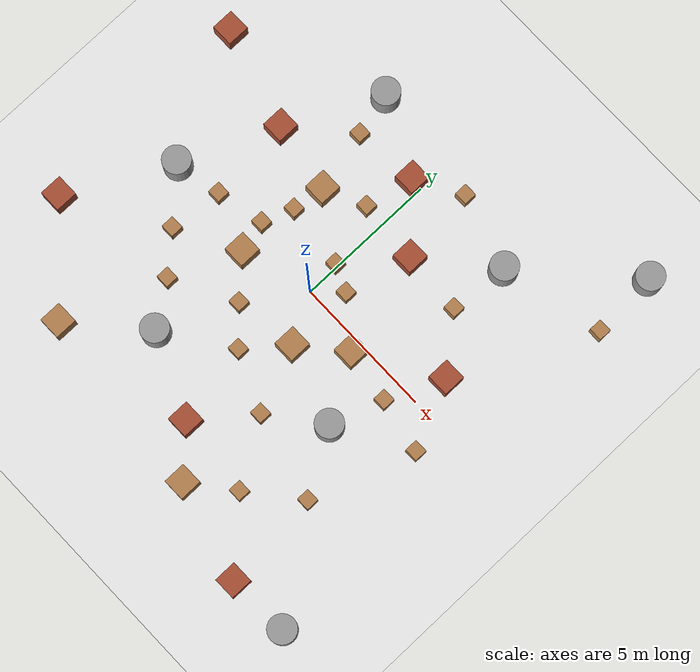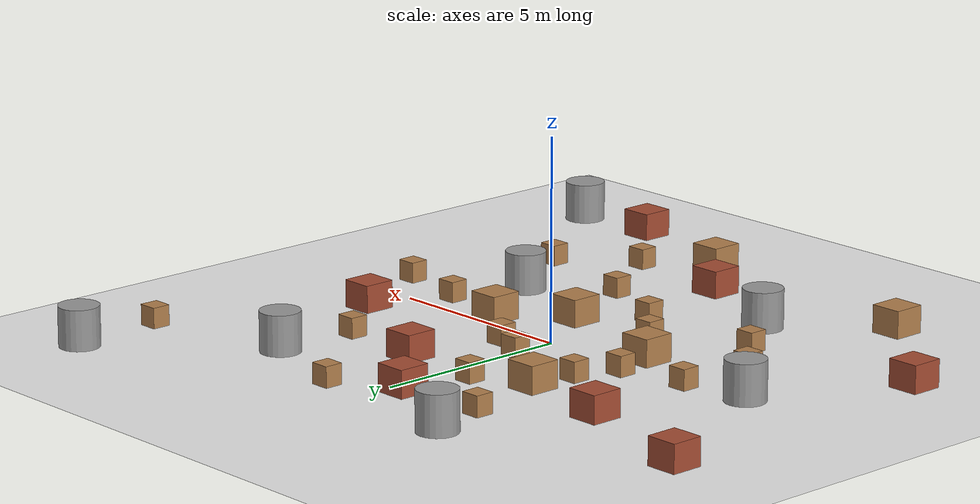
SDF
<sdf version="1.6">
 <world name="default">
  <light name="sun" type="directional">
   <pose>0 0 10 0 -0 0</pose>
   <diffuse>0.8 0.8 0.8 1</diffuse>
   <specular>0.1 0.1 0.1 1</specular>
   <attenuation>
    <range>1000</range>
    <constant>0.9</constant>
    <linear>0.01</linear>
    <quadratic>0.001</quadratic>
   </attenuation>
   <direction>-0.5 0.5 -1</direction>
  </light>
  <model name="ground_plane">
   <static>1</static>
   <link name="link">
    <collision name="collision">
     <geometry><plane><normal>0 0 1</normal><size>100 100</size></plane></geometry>
     <surface><friction><ode><mu>100</mu><mu2>50</mu2></ode></friction></surface>
    </collision>
    <visual name="visual">
     <cast_shadows>0</cast_shadows>
     <geometry><plane><normal>0 0 1</normal><size>100 100</size></plane></geometry>
     <material>
      <script><uri>file://media/materials/scripts/gazebo.material</uri><name>Gazebo/White</name></script>
     </material>
    </visual>
   </link>
  </model>
  <gravity>0 0 -9.8</gravity>
  <magnetic_field>6e-06 2.3e-05 -4.2e-05</magnetic_field>
  <atmosphere type="adiabatic"/>
  <physics name="default_physics" default="0" type="ode">
   <max_step_size>0.005</max_step_size>
   <real_time_factor>1</real_time_factor>
   <real_time_update_rate>1000</real_time_update_rate>
  </physics>
  <scene><ambient>0.4 0.4 0.4 1</ambient><background>1 1 1 1</background><shadows>1</shadows></scene>
  <spherical_coordinates>
   <surface_model>EARTH_WGS84</surface_model>
   <latitude_deg>0</latitude_deg>
   <longitude_deg>0</longitude_deg>
   <elevation>0</elevation>
   <heading_deg>0</heading_deg>
  </spherical_coordinates>
  <model name="Box">
   <link name="link">
    <inertial>
     <mass>0.01</mass>
     <inertia>
      <ixx>0.00455697</ixx>
      <ixy>0</ixy>
      <ixz>0</ixz>
      <iyy>0.00475558</iyy>
      <iyz>0</iyz>
      <izz>0.00426137</izz>
     </inertia>
    </inertial>
    <visual name="visual">
     <geometry><box><size>0.483208 0.461193 0.514245</size></box></geometry>
     <material>
      <script><name>Gazebo/WoodFloor</name><uri>file://media/materials/scripts/gazebo.material</uri></script>
      <ambient>0.3 0.3 0.3 1</ambient>
      <diffuse>0.7 0.7 0.7 1</diffuse>
      <specular>0.01 0.01 0.01 1</specular>
      <emissive>0 0 0 1</emissive>
     </material>
    </visual>
    <collision name="collision">
     <geometry><box><size>0.483208 0.461193 0.514245</size></box></geometry>
     <surface>
      <friction>
       <ode><mu>1</mu><mu2>1</mu2><fdir1>0 0 0</fdir1><slip1>0</slip1><slip2>0</slip2></ode>
       <torsional>
        <coefficient>1</coefficient>
        <patch_radius>0</patch_radius>
        <surface_radius>0</surface_radius>
        <use_patch_radius>1</use_patch_radius>
        <ode><slip>0</slip></ode>
       </torsional>
      </friction>
      <bounce><restitution_coefficient>0</restitution_coefficient><threshold>1e+06</threshold></bounce>
      <contact>
       <collide_without_contact>0</collide_without_contact>
       <collide_without_contact_bitmask>1</collide_without_contact_bitmask>
       <collide_bitmask>1</collide_bitmask>
       <ode>
        <soft_cfm>0</soft_cfm>
        <soft_erp>0.2</soft_erp>
        <kp>1e+13</kp>
        <kd>1</kd>
        <max_vel>0.01</max_vel>
        <min_depth>0</min_depth>
       </ode>
       <bullet>
        <split_impulse>1</split_impulse>
        <split_impulse_penetration_threshold>-0.01</split_impulse_penetration_threshold>
        <soft_cfm>0</soft_cfm>
        <soft_erp>0.2</soft_erp>
        <kp>1e+13</kp>
        <kd>1</kd>
       </bullet>
      </contact>
     </surface>
    </collision>
   </link>
   <static>0</static>
   <pose>-2.73541 0.399797 0.257122 0 -0 0</pose>
  </model>
  <model name="Box_0">
   <link name="link">
    <inertial>
     <mass>0.01</mass>
     <inertia>
      <ixx>0.00455697</ixx>
      <ixy>0</ixy>
      <ixz>0</ixz>
      <iyy>0.00475558</iyy>
      <iyz>0</iyz>
      <izz>0.00426137</izz>
     </inertia>
    </inertial>
    <visual name="visual">
     <geometry><box><size>0.483208 0.461193 0.514245</size></box></geometry>
     <material>
      <script><name>Gazebo/WoodFloor</name><uri>file://media/materials/scripts/gazebo.material</uri></script>
      <ambient>0.3 0.3 0.3 1</ambient>
      <diffuse>0.7 0.7 0.7 1</diffuse>
      <specular>0.01 0.01 0.01 1</specular>
      <emissive>0 0 0 1</emissive>
     </material>
    </visual>
    <collision name="collision">
     <geometry><box><size>0.483208 0.461193 0.514245</size></box></geometry>
     <surface>
      <friction>
       <ode><mu>1</mu><mu2>1</mu2><fdir1>0 0 0</fdir1><slip1>0</slip1><slip2>0</slip2></ode>
       <torsional>
        <coefficient>1</coefficient>
        <patch_radius>0</patch_radius>
        <surface_radius>0</surface_radius>
        <use_patch_radius>1</use_patch_radius>
        <ode><slip>0</slip></ode>
       </torsional>
      </friction>
      <bounce><restitution_coefficient>0</restitution_coefficient><threshold>1e+06</threshold></bounce>
      <contact>
       <collide_without_contact>0</collide_without_contact>
       <collide_without_contact_bitmask>1</collide_without_contact_bitmask>
       <collide_bitmask>1</collide_bitmask>
       <ode>
        <soft_cfm>0</soft_cfm>
        <soft_erp>0.2</soft_erp>
        <kp>1e+13</kp>
        <kd>1</kd>
        <max_vel>0.01</max_vel>
        <min_depth>0</min_depth>
       </ode>
       <bullet>
        <split_impulse>1</split_impulse>
        <split_impulse_penetration_threshold>-0.01</split_impulse_penetration_threshold>
        <soft_cfm>0</soft_cfm>
        <soft_erp>0.2</soft_erp>
        <kp>1e+13</kp>
        <kd>1</kd>
       </bullet>
      </contact>
     </surface>
    </collision>
   </link>
   <static>0</static>
   <pose>-1.29677 -1.94681 0.257122 0 -0 0</pose>
  </model>
  <model name="Box_1">
   <link name="link">
    <inertial>
     <mass>0.01</mass>
     <inertia>
      <ixx>0.00455697</ixx>
      <ixy>0</ixy>
      <ixz>0</ixz>
      <iyy>0.00475558</iyy>
      <iyz>0</iyz>
      <izz>0.00426137</izz>
     </inertia>
    </inertial>
    <visual name="visual">
     <geometry><box><size>0.483208 0.461193 0.514245</size></box></geometry>
     <material>
      <script><name>Gazebo/WoodFloor</name><uri>file://media/materials/scripts/gazebo.material</uri></script>
      <ambient>0.3 0.3 0.3 1</ambient>
      <diffuse>0.7 0.7 0.7 1</diffuse>
      <specular>0.01 0.01 0.01 1</specular>
      <emissive>0 0 0 1</emissive>
     </material>
    </visual>
    <collision name="collision">
     <geometry><box><size>0.483208 0.461193 0.514245</size></box></geometry>
     <surface>
      <friction>
       <ode><mu>1</mu><mu2>1</mu2><fdir1>0 0 0</fdir1><slip1>0</slip1><slip2>0</slip2></ode>
       <torsional>
        <coefficient>1</coefficient>
        <patch_radius>0</patch_radius>
        <surface_radius>0</surface_radius>
        <use_patch_radius>1</use_patch_radius>
        <ode><slip>0</slip></ode>
       </torsional>
      </friction>
      <bounce><restitution_coefficient>0</restitution_coefficient><threshold>1e+06</threshold></bounce>
      <contact>
       <collide_without_contact>0</collide_without_contact>
       <collide_without_contact_bitmask>1</collide_without_contact_bitmask>
       <collide_bitmask>1</collide_bitmask>
       <ode>
        <soft_cfm>0</soft_cfm>
        <soft_erp>0.2</soft_erp>
        <kp>1e+13</kp>
        <kd>1</kd>
        <max_vel>0.01</max_vel>
        <min_depth>0</min_depth>
       </ode>
       <bullet>
        <split_impulse>1</split_impulse>
        <split_impulse_penetration_threshold>-0.01</split_impulse_penetration_threshold>
        <soft_cfm>0</soft_cfm>
        <soft_erp>0.2</soft_erp>
        <kp>1e+13</kp>
        <kd>1</kd>
       </bullet>
      </contact>
     </surface>
    </collision>
   </link>
   <static>0</static>
   <pose>0.855063 0.802123 0.257122 0 -0 0</pose>
  </model>
  <model name="HeavyBox">
   <link name="link">
    <inertial>
     <mass>0.0579948</mass>
     <inertia>
      <ixx>0.0402452</ixx>
      <ixy>0</ixy>
      <ixz>0</ixz>
      <iyy>0.0399236</iyy>
      <iyz>0</iyz>
      <izz>0.0461707</izz>
     </inertia>
    </inertial>
    <visual name="visual">
     <geometry><box><size>0.79482 0.800386 0.684447</size></box></geometry>
     <material>
      <script><name>Gazebo/WoodFloor</name><uri>file://media/materials/scripts/gazebo.material</uri></script>
      <ambient>0.3 0.3 0.3 1</ambient>
      <diffuse>0.7 0.7 0.7 1</diffuse>
      <specular>0.01 0.01 0.01 1</specular>
      <emissive>0 0 0 1</emissive>
     </material>
    </visual>
    <collision name="collision">
     <geometry><box><size>0.79482 0.800386 0.684447</size></box></geometry>
     <surface>
      <friction>
       <ode><mu>1</mu><mu2>1</mu2><fdir1>0 0 0</fdir1><slip1>0</slip1><slip2>0</slip2></ode>
       <torsional>
        <coefficient>1</coefficient>
        <patch_radius>0</patch_radius>
        <surface_radius>0</surface_radius>
        <use_patch_radius>1</use_patch_radius>
        <ode><slip>0</slip></ode>
       </torsional>
      </friction>
      <bounce><restitution_coefficient>0</restitution_coefficient><threshold>1e+06</threshold></bounce>
      <contact>
       <collide_without_contact>0</collide_without_contact>
       <collide_without_contact_bitmask>1</collide_without_contact_bitmask>
       <collide_bitmask>1</collide_bitmask>
       <ode>
        <soft_cfm>0</soft_cfm>
        <soft_erp>0.2</soft_erp>
        <kp>1e+13</kp>
        <kd>1</kd>
        <max_vel>0.01</max_vel>
        <min_depth>0</min_depth>
       </ode>
       <bullet>
        <split_impulse>1</split_impulse>
        <split_impulse_penetration_threshold>-0.01</split_impulse_penetration_threshold>
        <soft_cfm>0</soft_cfm>
        <soft_erp>0.2</soft_erp>
        <kp>1e+13</kp>
        <kd>1</kd>
       </bullet>
      </contact>
     </surface>
    </collision>
   </link>
   <static>0</static>
   <pose>-2.17372 2.61263 0.342223 0 -0 0</pose>
  </model>
  <model name="HeavyBox_0">
   <link name="link">
    <inertial>
     <mass>0.0579948</mass>
     <inertia>
      <ixx>0.0402452</ixx>
      <ixy>0</ixy>
      <ixz>0</ixz>
      <iyy>0.0399236</iyy>
      <iyz>0</iyz>
      <izz>0.0461707</izz>
     </inertia>
    </inertial>
    <visual name="visual">
     <geometry><box><size>0.79482 0.800386 0.684447</size></box></geometry>
     <material>
      <script><name>Gazebo/WoodFloor</name><uri>file://media/materials/scripts/gazebo.material</uri></script>
      <ambient>0.3 0.3 0.3 1</ambient>
      <diffuse>0.7 0.7 0.7 1</diffuse>
      <specular>0.01 0.01 0.01 1</specular>
      <emissive>0 0 0 1</emissive>
     </material>
    </visual>
    <collision name="collision">
     <geometry><box><size>0.79482 0.800386 0.684447</size></box></geometry>
     <surface>
      <friction>
       <ode><mu>1</mu><mu2>1</mu2><fdir1>0 0 0</fdir1><slip1>0</slip1><slip2>0</slip2></ode>
       <torsional>
        <coefficient>1</coefficient>
        <patch_radius>0</patch_radius>
        <surface_radius>0</surface_radius>
        <use_patch_radius>1</use_patch_radius>
        <ode><slip>0</slip></ode>
       </torsional>
      </friction>
      <bounce><restitution_coefficient>0</restitution_coefficient><threshold>1e+06</threshold></bounce>
      <contact>
       <collide_without_contact>0</collide_without_contact>
       <collide_without_contact_bitmask>1</collide_without_contact_bitmask>
       <collide_bitmask>1</collide_bitmask>
       <ode>
        <soft_cfm>0</soft_cfm>
        <soft_erp>0.2</soft_erp>
        <kp>1e+13</kp>
        <kd>1</kd>
        <max_vel>0.01</max_vel>
        <min_depth>0</min_depth>
       </ode>
       <bullet>
        <split_impulse>1</split_impulse>
        <split_impulse_penetration_threshold>-0.01</split_impulse_penetration_threshold>
        <soft_cfm>0</soft_cfm>
        <soft_erp>0.2</soft_erp>
        <kp>1e+13</kp>
        <kd>1</kd>
       </bullet>
      </contact>
     </surface>
    </collision>
   </link>
   <static>0</static>
   <pose>-2.46098 -0.708765 0.342223 0 -0 0</pose>
  </model>
  <model name="HeavyBox_1">
   <link name="link">
    <inertial>
     <mass>0.0579948</mass>
     <inertia>
      <ixx>0.0402452</ixx>
      <ixy>0</ixy>
      <ixz>0</ixz>
      <iyy>0.0399236</iyy>
      <iyz>0</iyz>
      <izz>0.0461707</izz>
     </inertia>
    </inertial>
    <visual name="visual">
     <geometry><box><size>0.79482 0.800386 0.684447</size></box></geometry>
     <material>
      <script><name>Gazebo/WoodFloor</name><uri>file://media/materials/scripts/gazebo.material</uri></script>
      <ambient>0.3 0.3 0.3 1</ambient>
      <diffuse>0.7 0.7 0.7 1</diffuse>
      <specular>0.01 0.01 0.01 1</specular>
      <emissive>0 0 0 1</emissive>
     </material>
    </visual>
    <collision name="collision">
     <geometry><box><size>0.79482 0.800386 0.684447</size></box></geometry>
     <surface>
      <friction>
       <ode><mu>1</mu><mu2>1</mu2><fdir1>0 0 0</fdir1><slip1>0</slip1><slip2>0</slip2></ode>
       <torsional>
        <coefficient>1</coefficient>
        <patch_radius>0</patch_radius>
        <surface_radius>0</surface_radius>
        <use_patch_radius>1</use_patch_radius>
        <ode><slip>0</slip></ode>
       </torsional>
      </friction>
      <bounce><restitution_coefficient>0</restitution_coefficient><threshold>1e+06</threshold></bounce>
      <contact>
       <collide_without_contact>0</collide_without_contact>
       <collide_without_contact_bitmask>1</collide_without_contact_bitmask>
       <collide_bitmask>1</collide_bitmask>
       <ode>
        <soft_cfm>0</soft_cfm>
        <soft_erp>0.2</soft_erp>
        <kp>1e+13</kp>
        <kd>1</kd>
        <max_vel>0.01</max_vel>
        <min_depth>0</min_depth>
       </ode>
       <bullet>
        <split_impulse>1</split_impulse>
        <split_impulse_penetration_threshold>-0.01</split_impulse_penetration_threshold>
        <soft_cfm>0</soft_cfm>
        <soft_erp>0.2</soft_erp>
        <kp>1e+13</kp>
        <kd>1</kd>
       </bullet>
      </contact>
     </surface>
    </collision>
   </link>
   <static>0</static>
   <pose>0.92371 -1.65495 0.342223 0 -0 0</pose>
  </model>
  <model name="HeavyBox_2">
   <link name="link">
    <inertial>
     <mass>0.0579948</mass>
     <inertia>
      <ixx>0.0402452</ixx>
      <ixy>0</ixy>
      <ixz>0</ixz>
      <iyy>0.0399236</iyy>
      <iyz>0</iyz>
      <izz>0.0461707</izz>
     </inertia>
    </inertial>
    <visual name="visual">
     <geometry><box><size>0.79482 0.800386 0.684447</size></box></geometry>
     <material>
      <script><name>Gazebo/WoodFloor</name><uri>file://media/materials/scripts/gazebo.material</uri></script>
      <ambient>0.3 0.3 0.3 1</ambient>
      <diffuse>0.7 0.7 0.7 1</diffuse>
      <specular>0.01 0.01 0.01 1</specular>
      <emissive>0 0 0 1</emissive>
     </material>
    </visual>
    <collision name="collision">
     <geometry><box><size>0.79482 0.800386 0.684447</size></box></geometry>
     <surface>
      <friction>
       <ode><mu>1</mu><mu2>1</mu2><fdir1>0 0 0</fdir1><slip1>0</slip1><slip2>0</slip2></ode>
       <torsional>
        <coefficient>1</coefficient>
        <patch_radius>0</patch_radius>
        <surface_radius>0</surface_radius>
        <use_patch_radius>1</use_patch_radius>
        <ode><slip>0</slip></ode>
       </torsional>
      </friction>
      <bounce><restitution_coefficient>0</restitution_coefficient><threshold>1e+06</threshold></bounce>
      <contact>
       <collide_without_contact>0</collide_without_contact>
       <collide_without_contact_bitmask>1</collide_without_contact_bitmask>
       <collide_bitmask>1</collide_bitmask>
       <ode>
        <soft_cfm>0</soft_cfm>
        <soft_erp>0.2</soft_erp>
        <kp>1e+13</kp>
        <kd>1</kd>
        <max_vel>0.01</max_vel>
        <min_depth>0</min_depth>
       </ode>
       <bullet>
        <split_impulse>1</split_impulse>
        <split_impulse_penetration_threshold>-0.01</split_impulse_penetration_threshold>
        <soft_cfm>0</soft_cfm>
        <soft_erp>0.2</soft_erp>
        <kp>1e+13</kp>
        <kd>1</kd>
       </bullet>
      </contact>
     </surface>
    </collision>
   </link>
   <static>0</static>
   <pose>2.39174 -0.406976 0.342223 0 -0 0</pose>
  </model>
  <model name="Box_2">
   <link name="link">
    <inertial>
     <mass>0.01</mass>
     <inertia>
      <ixx>0.00455697</ixx>
      <ixy>0</ixy>
      <ixz>0</ixz>
      <iyy>0.00475558</iyy>
      <iyz>0</iyz>
      <izz>0.00426137</izz>
     </inertia>
    </inertial>
    <visual name="visual">
     <geometry><box><size>0.483208 0.461193 0.514245</size></box></geometry>
     <material>
      <script><name>Gazebo/WoodFloor</name><uri>file://media/materials/scripts/gazebo.material</uri></script>
      <ambient>0.3 0.3 0.3 1</ambient>
      <diffuse>0.7 0.7 0.7 1</diffuse>
      <specular>0.01 0.01 0.01 1</specular>
      <emissive>0 0 0 1</emissive>
     </material>
    </visual>
    <collision name="collision">
     <geometry><box><size>0.483208 0.461193 0.514245</size></box></geometry>
     <surface>
      <friction>
       <ode><mu>1</mu><mu2>1</mu2><fdir1>0 0 0</fdir1><slip1>0</slip1><slip2>0</slip2></ode>
       <torsional>
        <coefficient>1</coefficient>
        <patch_radius>0</patch_radius>
        <surface_radius>0</surface_radius>
        <use_patch_radius>1</use_patch_radius>
        <ode><slip>0</slip></ode>
       </torsional>
      </friction>
      <bounce><restitution_coefficient>0</restitution_coefficient><threshold>1e+06</threshold></bounce>
      <contact>
       <collide_without_contact>0</collide_without_contact>
       <collide_without_contact_bitmask>1</collide_without_contact_bitmask>
       <collide_bitmask>1</collide_bitmask>
       <ode>
        <soft_cfm>0</soft_cfm>
        <soft_erp>0.2</soft_erp>
        <kp>1e+13</kp>
        <kd>1</kd>
        <max_vel>0.01</max_vel>
        <min_depth>0</min_depth>
       </ode>
       <bullet>
        <split_impulse>1</split_impulse>
        <split_impulse_penetration_threshold>-0.01</split_impulse_penetration_threshold>
        <soft_cfm>0</soft_cfm>
        <soft_erp>0.2</soft_erp>
        <kp>1e+13</kp>
        <kd>1</kd>
       </bullet>
      </contact>
     </surface>
    </collision>
   </link>
   <static>0</static>
   <pose>-2.33619 1.48041 0.257122 0 -0 0</pose>
  </model>
  <model name="Box_3">
   <link name="link">
    <inertial>
     <mass>0.01</mass>
     <inertia>
      <ixx>0.00455697</ixx>
      <ixy>0</ixy>
      <ixz>0</ixz>
      <iyy>0.00475558</iyy>
      <iyz>0</iyz>
      <izz>0.00426137</izz>
     </inertia>
    </inertial>
    <visual name="visual">
     <geometry><box><size>0.483208 0.461193 0.514245</size></box></geometry>
     <material>
      <script><name>Gazebo/WoodFloor</name><uri>file://media/materials/scripts/gazebo.material</uri></script>
      <ambient>0.3 0.3 0.3 1</ambient>
      <diffuse>0.7 0.7 0.7 1</diffuse>
      <specular>0.01 0.01 0.01 1</specular>
      <emissive>0 0 0 1</emissive>
     </material>
    </visual>
    <collision name="collision">
     <geometry><box><size>0.483208 0.461193 0.514245</size></box></geometry>
     <surface>
      <friction>
       <ode><mu>1</mu><mu2>1</mu2><fdir1>0 0 0</fdir1><slip1>0</slip1><slip2>0</slip2></ode>
       <torsional>
        <coefficient>1</coefficient>
        <patch_radius>0</patch_radius>
        <surface_radius>0</surface_radius>
        <use_patch_radius>1</use_patch_radius>
        <ode><slip>0</slip></ode>
       </torsional>
      </friction>
      <bounce><restitution_coefficient>0</restitution_coefficient><threshold>1e+06</threshold></bounce>
      <contact>
       <collide_without_contact>0</collide_without_contact>
       <collide_without_contact_bitmask>1</collide_without_contact_bitmask>
       <collide_bitmask>1</collide_bitmask>
       <ode>
        <soft_cfm>0</soft_cfm>
        <soft_erp>0.2</soft_erp>
        <kp>1e+13</kp>
        <kd>1</kd>
        <max_vel>0.01</max_vel>
        <min_depth>0</min_depth>
       </ode>
       <bullet>
        <split_impulse>1</split_impulse>
        <split_impulse_penetration_threshold>-0.01</split_impulse_penetration_threshold>
        <soft_cfm>0</soft_cfm>
        <soft_erp>0.2</soft_erp>
        <kp>1e+13</kp>
        <kd>1</kd>
       </bullet>
      </contact>
     </surface>
    </collision>
   </link>
   <static>0</static>
   <pose>-0.078578 1.21617 0.257122 0 -0 0</pose>
  </model>
  <model name="HighRock">
   <link name="link_0">
    <inertial>
     <mass>5</mass>
     <inertia><ixx>0.145833</ixx><ixy>0</ixy><ixz>0</ixz><iyy>0.145833</iyy><iyz>0</iyz><izz>0.125</izz></inertia>
    </inertial>
    <visual name="visual">
     <geometry><cylinder><radius>0.5</radius><length>1</length></cylinder></geometry>
     <material>
      <lighting>1</lighting>
      <script><uri>file://media/materials/scripts/gazebo.material</uri><name>Gazebo/Gray</name></script>
      <ambient>0.3 0.3 0.3 1</ambient>
      <diffuse>0.7 0.7 0.7 1</diffuse>
      <specular>0.01 0.01 0.01 1</specular>
      <emissive>0 0 0 1</emissive>
     </material>
    </visual>
    <collision name="collision">
     <geometry><cylinder><radius>0.5</radius><length>1</length></cylinder></geometry>
     <surface>
      <friction>
       <ode><mu>1</mu><mu2>1</mu2><fdir1>0 0 0</fdir1><slip1>0</slip1><slip2>0</slip2></ode>
       <torsional>
        <coefficient>1</coefficient>
        <patch_radius>0</patch_radius>
        <surface_radius>0</surface_radius>
        <use_patch_radius>1</use_patch_radius>
        <ode><slip>0</slip></ode>
       </torsional>
      </friction>
      <bounce><restitution_coefficient>0</restitution_coefficient><threshold>1e+06</threshold></bounce>
      <contact>
       <collide_without_contact>0</collide_without_contact>
       <collide_without_contact_bitmask>1</collide_without_contact_bitmask>
       <collide_bitmask>1</collide_bitmask>
       <ode>
        <soft_cfm>0</soft_cfm>
        <soft_erp>0.2</soft_erp>
        <kp>1e+13</kp>
        <kd>1</kd>
        <max_vel>0.01</max_vel>
        <min_depth>0</min_depth>
       </ode>
       <bullet>
        <split_impulse>1</split_impulse>
        <split_impulse_penetration_threshold>-0.01</split_impulse_penetration_threshold>
        <soft_cfm>0</soft_cfm>
        <soft_erp>0.2</soft_erp>
        <kp>1e+13</kp>
        <kd>1</kd>
       </bullet>
      </contact>
     </surface>
    </collision>
   </link>
   <static>0</static>
   <pose>-2.45158 -4.55607 0.499999 0 0 -1e-06</pose>
  </model>
  <model name="HeavyBox_3">
   <link name="link">
    <inertial>
     <mass>2</mass>
     <inertia>
      <ixx>0.0402452</ixx>
      <ixy>0</ixy>
      <ixz>0</ixz>
      <iyy>0.0399236</iyy>
      <iyz>0</iyz>
      <izz>0.0461707</izz>
     </inertia>
    </inertial>
    <visual name="visual">
     <geometry><box><size>0.79482 0.800386 0.684447</size></box></geometry>
     <material>
      <script><name>Gazebo/Bricks</name><uri>file://media/materials/scripts/gazebo.material</uri></script>
      <ambient>0.3 0.3 0.3 1</ambient>
      <diffuse>0.7 0.7 0.7 1</diffuse>
      <specular>0.01 0.01 0.01 1</specular>
      <emissive>0 0 0 1</emissive>
     </material>
    </visual>
    <collision name="collision">
     <geometry><box><size>0.79482 0.800386 0.684447</size></box></geometry>
     <surface>
      <friction>
       <ode><mu>1</mu><mu2>1</mu2><fdir1>0 0 0</fdir1><slip1>0</slip1><slip2>0</slip2></ode>
       <torsional>
        <coefficient>1</coefficient>
        <patch_radius>0</patch_radius>
        <surface_radius>0</surface_radius>
        <use_patch_radius>1</use_patch_radius>
        <ode><slip>0</slip></ode>
       </torsional>
      </friction>
      <bounce><restitution_coefficient>0</restitution_coefficient><threshold>1e+06</threshold></bounce>
      <contact>
       <collide_without_contact>0</collide_without_contact>
       <collide_without_contact_bitmask>1</collide_without_contact_bitmask>
       <collide_bitmask>1</collide_bitmask>
       <ode>
        <soft_cfm>0</soft_cfm>
        <soft_erp>0.2</soft_erp>
        <kp>1e+13</kp>
        <kd>1</kd>
        <max_vel>0.01</max_vel>
        <min_depth>0</min_depth>
       </ode>
       <bullet>
        <split_impulse>1</split_impulse>
        <split_impulse_penetration_threshold>-0.01</split_impulse_penetration_threshold>
        <soft_cfm>0</soft_cfm>
        <soft_erp>0.2</soft_erp>
        <kp>1e+13</kp>
        <kd>1</kd>
       </bullet>
      </contact>
     </surface>
    </collision>
   </link>
   <static>0</static>
   <pose>-0.407093 4.96879 0.342224 -0 -1e-06 9.8e-05</pose>
  </model>
  <model name="HeavyBox_4">
   <link name="link">
    <inertial>
     <mass>2</mass>
     <inertia>
      <ixx>0.0402452</ixx>
      <ixy>0</ixy>
      <ixz>0</ixz>
      <iyy>0.0399236</iyy>
      <iyz>0</iyz>
      <izz>0.0461707</izz>
     </inertia>
    </inertial>
    <visual name="visual">
     <geometry><box><size>0.79482 0.800386 0.684447</size></box></geometry>
     <material>
      <script><name>Gazebo/Bricks</name><uri>file://media/materials/scripts/gazebo.material</uri></script>
      <ambient>0.3 0.3 0.3 1</ambient>
      <diffuse>0.7 0.7 0.7 1</diffuse>
      <specular>0.01 0.01 0.01 1</specular>
      <emissive>0 0 0 1</emissive>
     </material>
    </visual>
    <collision name="collision">
     <geometry><box><size>0.79482 0.800386 0.684447</size></box></geometry>
     <surface>
      <friction>
       <ode><mu>1</mu><mu2>1</mu2><fdir1>0 0 0</fdir1><slip1>0</slip1><slip2>0</slip2></ode>
       <torsional>
        <coefficient>1</coefficient>
        <patch_radius>0</patch_radius>
        <surface_radius>0</surface_radius>
        <use_patch_radius>1</use_patch_radius>
        <ode><slip>0</slip></ode>
       </torsional>
      </friction>
      <bounce><restitution_coefficient>0</restitution_coefficient><threshold>1e+06</threshold></bounce>
      <contact>
       <collide_without_contact>0</collide_without_contact>
       <collide_without_contact_bitmask>1</collide_without_contact_bitmask>
       <collide_bitmask>1</collide_bitmask>
       <ode>
        <soft_cfm>0</soft_cfm>
        <soft_erp>0.2</soft_erp>
        <kp>1e+13</kp>
        <kd>1</kd>
        <max_vel>0.01</max_vel>
        <min_depth>0</min_depth>
       </ode>
       <bullet>
        <split_impulse>1</split_impulse>
        <split_impulse_penetration_threshold>-0.01</split_impulse_penetration_threshold>
        <soft_cfm>0</soft_cfm>
        <soft_erp>0.2</soft_erp>
        <kp>1e+13</kp>
        <kd>1</kd>
       </bullet>
      </contact>
     </surface>
    </collision>
   </link>
   <static>0</static>
   <pose>1.45059 3.10798 0.342219 -0 1.1e-05 9.5e-05</pose>
  </model>
  <model name="Box_4">
   <link name="link">
    <inertial>
     <mass>0.01</mass>
     <inertia>
      <ixx>0.00455697</ixx>
      <ixy>0</ixy>
      <ixz>0</ixz>
      <iyy>0.00475558</iyy>
      <iyz>0</iyz>
      <izz>0.00426137</izz>
     </inertia>
    </inertial>
    <visual name="visual">
     <geometry><box><size>0.483208 0.461193 0.514245</size></box></geometry>
     <material>
      <script><name>Gazebo/WoodFloor</name><uri>file://media/materials/scripts/gazebo.material</uri></script>
      <ambient>0.3 0.3 0.3 1</ambient>
      <diffuse>0.7 0.7 0.7 1</diffuse>
      <specular>0.01 0.01 0.01 1</specular>
      <emissive>0 0 0 1</emissive>
     </material>
    </visual>
    <collision name="collision">
     <geometry><box><size>0.483208 0.461193 0.514245</size></box></geometry>
     <surface>
      <friction>
       <ode><mu>1</mu><mu2>1</mu2><fdir1>0 0 0</fdir1><slip1>0</slip1><slip2>0</slip2></ode>
       <torsional>
        <coefficient>1</coefficient>
        <patch_radius>0</patch_radius>
        <surface_radius>0</surface_radius>
        <use_patch_radius>1</use_patch_radius>
        <ode><slip>0</slip></ode>
       </torsional>
      </friction>
      <bounce><restitution_coefficient>0</restitution_coefficient><threshold>1e+06</threshold></bounce>
      <contact>
       <collide_without_contact>0</collide_without_contact>
       <collide_without_contact_bitmask>1</collide_without_contact_bitmask>
       <collide_bitmask>1</collide_bitmask>
       <ode>
        <soft_cfm>0</soft_cfm>
        <soft_erp>0.2</soft_erp>
        <kp>1e+13</kp>
        <kd>1</kd>
        <max_vel>0.01</max_vel>
        <min_depth>0</min_depth>
       </ode>
       <bullet>
        <split_impulse>1</split_impulse>
        <split_impulse_penetration_threshold>-0.01</split_impulse_penetration_threshold>
        <soft_cfm>0</soft_cfm>
        <soft_erp>0.2</soft_erp>
        <kp>1e+13</kp>
        <kd>1</kd>
       </bullet>
      </contact>
     </surface>
    </collision>
   </link>
   <static>0</static>
   <pose>-0.187064 -3.01176 0.257122 0 -0 0</pose>
  </model>
  <model name="Box_5">
   <link name="link">
    <inertial>
     <mass>0.01</mass>
     <inertia>
      <ixx>0.00455697</ixx>
      <ixy>0</ixy>
      <ixz>0</ixz>
      <iyy>0.00475558</iyy>
      <iyz>0</iyz>
      <izz>0.00426137</izz>
     </inertia>
    </inertial>
    <visual name="visual">
     <geometry><box><size>0.483208 0.461193 0.514245</size></box></geometry>
     <material>
      <script><name>Gazebo/WoodFloor</name><uri>file://media/materials/scripts/gazebo.material</uri></script>
      <ambient>0.3 0.3 0.3 1</ambient>
      <diffuse>0.7 0.7 0.7 1</diffuse>
      <specular>0.01 0.01 0.01 1</specular>
      <emissive>0 0 0 1</emissive>
     </material>
    </visual>
    <collision name="collision">
     <geometry><box><size>0.483208 0.461193 0.514245</size></box></geometry>
     <surface>
      <friction>
       <ode><mu>1</mu><mu2>1</mu2><fdir1>0 0 0</fdir1><slip1>0</slip1><slip2>0</slip2></ode>
       <torsional>
        <coefficient>1</coefficient>
        <patch_radius>0</patch_radius>
        <surface_radius>0</surface_radius>
        <use_patch_radius>1</use_patch_radius>
        <ode><slip>0</slip></ode>
       </torsional>
      </friction>
      <bounce><restitution_coefficient>0</restitution_coefficient><threshold>1e+06</threshold></bounce>
      <contact>
       <collide_without_contact>0</collide_without_contact>
       <collide_without_contact_bitmask>1</collide_without_contact_bitmask>
       <collide_bitmask>1</collide_bitmask>
       <ode>
        <soft_cfm>0</soft_cfm>
        <soft_erp>0.2</soft_erp>
        <kp>1e+13</kp>
        <kd>1</kd>
        <max_vel>0.01</max_vel>
        <min_depth>0</min_depth>
       </ode>
       <bullet>
        <split_impulse>1</split_impulse>
        <split_impulse_penetration_threshold>-0.01</split_impulse_penetration_threshold>
        <soft_cfm>0</soft_cfm>
        <soft_erp>0.2</soft_erp>
        <kp>1e+13</kp>
        <kd>1</kd>
       </bullet>
      </contact>
     </surface>
    </collision>
   </link>
   <static>0</static>
   <pose>-3.49282 -3.09166 0.257122 0 -0 0</pose>
  </model>
  <model name="HighRock_0">
   <link name="link_0">
    <inertial>
     <mass>5</mass>
     <inertia><ixx>0.145833</ixx><ixy>0</ixy><ixz>0</ixz><iyy>0.145833</iyy><iyz>0</iyz><izz>0.125</izz></inertia>
    </inertial>
    <visual name="visual">
     <geometry><cylinder><radius>0.5</radius><length>1</length></cylinder></geometry>
     <material>
      <lighting>1</lighting>
      <script><uri>file://media/materials/scripts/gazebo.material</uri><name>Gazebo/Gray</name></script>
      <ambient>0.3 0.3 0.3 1</ambient>
      <diffuse>0.7 0.7 0.7 1</diffuse>
      <specular>0.01 0.01 0.01 1</specular>
      <emissive>0 0 0 1</emissive>
     </material>
    </visual>
    <collision name="collision">
     <geometry><cylinder><radius>0.5</radius><length>1</length></cylinder></geometry>
     <surface>
      <friction>
       <ode><mu>1</mu><mu2>1</mu2><fdir1>0 0 0</fdir1><slip1>0</slip1><slip2>0</slip2></ode>
       <torsional>
        <coefficient>1</coefficient>
        <patch_radius>0</patch_radius>
        <surface_radius>0</surface_radius>
        <use_patch_radius>1</use_patch_radius>
        <ode><slip>0</slip></ode>
       </torsional>
      </friction>
      <bounce><restitution_coefficient>0</restitution_coefficient><threshold>1e+06</threshold></bounce>
      <contact>
       <collide_without_contact>0</collide_without_contact>
       <collide_without_contact_bitmask>1</collide_without_contact_bitmask>
       <collide_bitmask>1</collide_bitmask>
       <ode>
        <soft_cfm>0</soft_cfm>
        <soft_erp>0.2</soft_erp>
        <kp>1e+13</kp>
        <kd>1</kd>
        <max_vel>0.01</max_vel>
        <min_depth>0</min_depth>
       </ode>
       <bullet>
        <split_impulse>1</split_impulse>
        <split_impulse_penetration_threshold>-0.01</split_impulse_penetration_threshold>
        <soft_cfm>0</soft_cfm>
        <soft_erp>0.2</soft_erp>
        <kp>1e+13</kp>
        <kd>1</kd>
       </bullet>
      </contact>
     </surface>
    </collision>
   </link>
   <static>0</static>
   <pose>-6.0472 -0.275243 0.499991 -1e-06 1e-06 -1e-06</pose>
  </model>
  <model name="HighRock_1">
   <link name="link_0">
    <inertial>
     <mass>5</mass>
     <inertia><ixx>0.145833</ixx><ixy>0</ixy><ixz>0</ixz><iyy>0.145833</iyy><iyz>0</iyz><izz>0.125</izz></inertia>
    </inertial>
    <visual name="visual">
     <geometry><cylinder><radius>0.5</radius><length>1</length></cylinder></geometry>
     <material>
      <lighting>1</lighting>
      <script><uri>file://media/materials/scripts/gazebo.material</uri><name>Gazebo/Gray</name></script>
      <ambient>0.3 0.3 0.3 1</ambient>
      <diffuse>0.7 0.7 0.7 1</diffuse>
      <specular>0.01 0.01 0.01 1</specular>
      <emissive>0 0 0 1</emissive>
     </material>
    </visual>
    <collision name="collision">
     <geometry><cylinder><radius>0.5</radius><length>1</length></cylinder></geometry>
     <surface>
      <friction>
       <ode><mu>1</mu><mu2>1</mu2><fdir1>0 0 0</fdir1><slip1>0</slip1><slip2>0</slip2></ode>
       <torsional>
        <coefficient>1</coefficient>
        <patch_radius>0</patch_radius>
        <surface_radius>0</surface_radius>
        <use_patch_radius>1</use_patch_radius>
        <ode><slip>0</slip></ode>
       </torsional>
      </friction>
      <bounce><restitution_coefficient>0</restitution_coefficient><threshold>1e+06</threshold></bounce>
      <contact>
       <collide_without_contact>0</collide_without_contact>
       <collide_without_contact_bitmask>1</collide_without_contact_bitmask>
       <collide_bitmask>1</collide_bitmask>
       <ode>
        <soft_cfm>0</soft_cfm>
        <soft_erp>0.2</soft_erp>
        <kp>1e+13</kp>
        <kd>1</kd>
        <max_vel>0.01</max_vel>
        <min_depth>0</min_depth>
       </ode>
       <bullet>
        <split_impulse>1</split_impulse>
        <split_impulse_penetration_threshold>-0.01</split_impulse_penetration_threshold>
        <soft_cfm>0</soft_cfm>
        <soft_erp>0.2</soft_erp>
        <kp>1e+13</kp>
        <kd>1</kd>
       </bullet>
      </contact>
     </surface>
    </collision>
   </link>
   <static>0</static>
   <pose>3.66593 -2.58503 0.499999 1e-06 -0 -1e-06</pose>
  </model>
  <model name="HighRock_2">
   <link name="link_0">
    <inertial>
     <mass>5</mass>
     <inertia><ixx>0.145833</ixx><ixy>0</ixy><ixz>0</ixz><iyy>0.145833</iyy><iyz>0</iyz><izz>0.125</izz></inertia>
    </inertial>
    <visual name="visual">
     <geometry><cylinder><radius>0.5</radius><length>1</length></cylinder></geometry>
     <material>
      <lighting>1</lighting>
      <script><uri>file://media/materials/scripts/gazebo.material</uri><name>Gazebo/Gray</name></script>
      <ambient>0.3 0.3 0.3 1</ambient>
      <diffuse>0.7 0.7 0.7 1</diffuse>
      <specular>0.01 0.01 0.01 1</specular>
      <emissive>0 0 0 1</emissive>
     </material>
    </visual>
    <collision name="collision">
     <geometry><cylinder><radius>0.5</radius><length>1</length></cylinder></geometry>
     <surface>
      <friction>
       <ode><mu>1</mu><mu2>1</mu2><fdir1>0 0 0</fdir1><slip1>0</slip1><slip2>0</slip2></ode>
       <torsional>
        <coefficient>1</coefficient>
        <patch_radius>0</patch_radius>
        <surface_radius>0</surface_radius>
        <use_patch_radius>1</use_patch_radius>
        <ode><slip>0</slip></ode>
       </torsional>
      </friction>
      <bounce><restitution_coefficient>0</restitution_coefficient><threshold>1e+06</threshold></bounce>
      <contact>
       <collide_without_contact>0</collide_without_contact>
       <collide_without_contact_bitmask>1</collide_without_contact_bitmask>
       <collide_bitmask>1</collide_bitmask>
       <ode>
        <soft_cfm>0</soft_cfm>
        <soft_erp>0.2</soft_erp>
        <kp>1e+13</kp>
        <kd>1</kd>
        <max_vel>0.01</max_vel>
        <min_depth>0</min_depth>
       </ode>
       <bullet>
        <split_impulse>1</split_impulse>
        <split_impulse_penetration_threshold>-0.01</split_impulse_penetration_threshold>
        <soft_cfm>0</soft_cfm>
        <soft_erp>0.2</soft_erp>
        <kp>1e+13</kp>
        <kd>1</kd>
       </bullet>
      </contact>
     </surface>
    </collision>
   </link>
   <static>0</static>
   <pose>3.82885 5.04476 0.499991 -1e-06 -0 -1e-06</pose>
  </model>
  <model name="HighRock_3">
   <link name="link_0">
    <inertial>
     <mass>5</mass>
     <inertia><ixx>0.145833</ixx><ixy>0</ixy><ixz>0</ixz><iyy>0.145833</iyy><iyz>0</iyz><izz>0.125</izz></inertia>
    </inertial>
    <visual name="visual">
     <geometry><cylinder><radius>0.5</radius><length>1</length></cylinder></geometry>
     <material>
      <lighting>1</lighting>
      <script><uri>file://media/materials/scripts/gazebo.material</uri><name>Gazebo/Gray</name></script>
      <ambient>0.3 0.3 0.3 1</ambient>
      <diffuse>0.7 0.7 0.7 1</diffuse>
      <specular>0.01 0.01 0.01 1</specular>
      <emissive>0 0 0 1</emissive>
     </material>
    </visual>
    <collision name="collision">
     <geometry><cylinder><radius>0.5</radius><length>1</length></cylinder></geometry>
     <surface>
      <friction>
       <ode><mu>1</mu><mu2>1</mu2><fdir1>0 0 0</fdir1><slip1>0</slip1><slip2>0</slip2></ode>
       <torsional>
        <coefficient>1</coefficient>
        <patch_radius>0</patch_radius>
        <surface_radius>0</surface_radius>
        <use_patch_radius>1</use_patch_radius>
        <ode><slip>0</slip></ode>
       </torsional>
      </friction>
      <bounce><restitution_coefficient>0</restitution_coefficient><threshold>1e+06</threshold></bounce>
      <contact>
       <collide_without_contact>0</collide_without_contact>
       <collide_without_contact_bitmask>1</collide_without_contact_bitmask>
       <collide_bitmask>1</collide_bitmask>
       <ode>
        <soft_cfm>0</soft_cfm>
        <soft_erp>0.2</soft_erp>
        <kp>1e+13</kp>
        <kd>1</kd>
        <max_vel>0.01</max_vel>
        <min_depth>0</min_depth>
       </ode>
       <bullet>
        <split_impulse>1</split_impulse>
        <split_impulse_penetration_threshold>-0.01</split_impulse_penetration_threshold>
        <soft_cfm>0</soft_cfm>
        <soft_erp>0.2</soft_erp>
        <kp>1e+13</kp>
        <kd>1</kd>
       </bullet>
      </contact>
     </surface>
    </collision>
   </link>
   <static>0</static>
   <pose>-3.03058 6.26791 0.499999 0 0 -1e-06</pose>
  </model>
  <model name="HeavyBox_5">
   <link name="link">
    <inertial>
     <mass>2</mass>
     <inertia>
      <ixx>0.0402452</ixx>
      <ixy>0</ixy>
      <ixz>0</ixz>
      <iyy>0.0399236</iyy>
      <iyz>0</iyz>
      <izz>0.0461707</izz>
     </inertia>
    </inertial>
    <visual name="visual">
     <geometry><box><size>0.79482 0.800386 0.684447</size></box></geometry>
     <material>
      <script><name>Gazebo/Bricks</name><uri>file://media/materials/scripts/gazebo.material</uri></script>
      <ambient>0.3 0.3 0.3 1</ambient>
      <diffuse>0.7 0.7 0.7 1</diffuse>
      <specular>0.01 0.01 0.01 1</specular>
      <emissive>0 0 0 1</emissive>
     </material>
    </visual>
    <collision name="collision">
     <geometry><box><size>0.79482 0.800386 0.684447</size></box></geometry>
     <surface>
      <friction>
       <ode><mu>1</mu><mu2>1</mu2><fdir1>0 0 0</fdir1><slip1>0</slip1><slip2>0</slip2></ode>
       <torsional>
        <coefficient>1</coefficient>
        <patch_radius>0</patch_radius>
        <surface_radius>0</surface_radius>
        <use_patch_radius>1</use_patch_radius>
        <ode><slip>0</slip></ode>
       </torsional>
      </friction>
      <bounce><restitution_coefficient>0</restitution_coefficient><threshold>1e+06</threshold></bounce>
      <contact>
       <collide_without_contact>0</collide_without_contact>
       <collide_without_contact_bitmask>1</collide_without_contact_bitmask>
       <collide_bitmask>1</collide_bitmask>
       <ode>
        <soft_cfm>0</soft_cfm>
        <soft_erp>0.2</soft_erp>
        <kp>1e+13</kp>
        <kd>1</kd>
        <max_vel>0.01</max_vel>
        <min_depth>0</min_depth>
       </ode>
       <bullet>
        <split_impulse>1</split_impulse>
        <split_impulse_penetration_threshold>-0.01</split_impulse_penetration_threshold>
        <soft_cfm>0</soft_cfm>
        <soft_erp>0.2</soft_erp>
        <kp>1e+13</kp>
        <kd>1</kd>
       </bullet>
      </contact>
     </surface>
    </collision>
   </link>
   <static>0</static>
   <pose>-4.63867 3.03846 0.342224 0 -1e-06 7.1e-05</pose>
  </model>
  <model name="HeavyBox_6">
   <link name="link">
    <inertial>
     <mass>2</mass>
     <inertia>
      <ixx>0.0402452</ixx>
      <ixy>0</ixy>
      <ixz>0</ixz>
      <iyy>0.0399236</iyy>
      <iyz>0</iyz>
      <izz>0.0461707</izz>
     </inertia>
    </inertial>
    <visual name="visual">
     <geometry><box><size>0.79482 0.800386 0.684447</size></box></geometry>
     <material>
      <script><name>Gazebo/Bricks</name><uri>file://media/materials/scripts/gazebo.material</uri></script>
      <ambient>0.3 0.3 0.3 1</ambient>
      <diffuse>0.7 0.7 0.7 1</diffuse>
      <specular>0.01 0.01 0.01 1</specular>
      <emissive>0 0 0 1</emissive>
     </material>
    </visual>
    <collision name="collision">
     <geometry><box><size>0.79482 0.800386 0.684447</size></box></geometry>
     <surface>
      <friction>
       <ode><mu>1</mu><mu2>1</mu2><fdir1>0 0 0</fdir1><slip1>0</slip1><slip2>0</slip2></ode>
       <torsional>
        <coefficient>1</coefficient>
        <patch_radius>0</patch_radius>
        <surface_radius>0</surface_radius>
        <use_patch_radius>1</use_patch_radius>
        <ode><slip>0</slip></ode>
       </torsional>
      </friction>
      <bounce><restitution_coefficient>0</restitution_coefficient><threshold>1e+06</threshold></bounce>
      <contact>
       <collide_without_contact>0</collide_without_contact>
       <collide_without_contact_bitmask>1</collide_without_contact_bitmask>
       <collide_bitmask>1</collide_bitmask>
       <ode>
        <soft_cfm>0</soft_cfm>
        <soft_erp>0.2</soft_erp>
        <kp>1e+13</kp>
        <kd>1</kd>
        <max_vel>0.01</max_vel>
        <min_depth>0</min_depth>
       </ode>
       <bullet>
        <split_impulse>1</split_impulse>
        <split_impulse_penetration_threshold>-0.01</split_impulse_penetration_threshold>
        <soft_cfm>0</soft_cfm>
        <soft_erp>0.2</soft_erp>
        <kp>1e+13</kp>
        <kd>1</kd>
       </bullet>
      </contact>
     </surface>
    </collision>
   </link>
   <static>0</static>
   <pose>0.361489 -5.82049 0.342219 0 1.1e-05 6.8e-05</pose>
  </model>
  <model name="HeavyBox_7">
   <link name="link">
    <inertial>
     <mass>2</mass>
     <inertia>
      <ixx>0.0402452</ixx>
      <ixy>0</ixy>
      <ixz>0</ixz>
      <iyy>0.0399236</iyy>
      <iyz>0</iyz>
      <izz>0.0461707</izz>
     </inertia>
    </inertial>
    <visual name="visual">
     <geometry><box><size>0.79482 0.800386 0.684447</size></box></geometry>
     <material>
      <script><name>Gazebo/Bricks</name><uri>file://media/materials/scripts/gazebo.material</uri></script>
      <ambient>0.3 0.3 0.3 1</ambient>
      <diffuse>0.7 0.7 0.7 1</diffuse>
      <specular>0.01 0.01 0.01 1</specular>
      <emissive>0 0 0 1</emissive>
     </material>
    </visual>
    <collision name="collision">
     <geometry><box><size>0.79482 0.800386 0.684447</size></box></geometry>
     <surface>
      <friction>
       <ode><mu>1</mu><mu2>1</mu2><fdir1>0 0 0</fdir1><slip1>0</slip1><slip2>0</slip2></ode>
       <torsional>
        <coefficient>1</coefficient>
        <patch_radius>0</patch_radius>
        <surface_radius>0</surface_radius>
        <use_patch_radius>1</use_patch_radius>
        <ode><slip>0</slip></ode>
       </torsional>
      </friction>
      <bounce><restitution_coefficient>0</restitution_coefficient><threshold>1e+06</threshold></bounce>
      <contact>
       <collide_without_contact>0</collide_without_contact>
       <collide_without_contact_bitmask>1</collide_without_contact_bitmask>
       <collide_bitmask>1</collide_bitmask>
       <ode>
        <soft_cfm>0</soft_cfm>
        <soft_erp>0.2</soft_erp>
        <kp>1e+13</kp>
        <kd>1</kd>
        <max_vel>0.01</max_vel>
        <min_depth>0</min_depth>
       </ode>
       <bullet>
        <split_impulse>1</split_impulse>
        <split_impulse_penetration_threshold>-0.01</split_impulse_penetration_threshold>
        <soft_cfm>0</soft_cfm>
        <soft_erp>0.2</soft_erp>
        <kp>1e+13</kp>
        <kd>1</kd>
       </bullet>
      </contact>
     </surface>
    </collision>
   </link>
   <static>0</static>
   <pose>5.12892 1.20649 0.342224 0 1e-06 6.4e-05</pose>
  </model>
  <model name="Box_6">
   <link name="link">
    <inertial>
     <mass>0.01</mass>
     <inertia>
      <ixx>0.00455697</ixx>
      <ixy>0</ixy>
      <ixz>0</ixz>
      <iyy>0.00475558</iyy>
      <iyz>0</iyz>
      <izz>0.00426137</izz>
     </inertia>
    </inertial>
    <visual name="visual">
     <geometry><box><size>0.483208 0.461193 0.514245</size></box></geometry>
     <material>
      <script><name>Gazebo/WoodFloor</name><uri>file://media/materials/scripts/gazebo.material</uri></script>
      <ambient>0.3 0.3 0.3 1</ambient>
      <diffuse>0.7 0.7 0.7 1</diffuse>
      <specular>0.01 0.01 0.01 1</specular>
      <emissive>0 0 0 1</emissive>
     </material>
    </visual>
    <collision name="collision">
     <geometry><box><size>0.483208 0.461193 0.514245</size></box></geometry>
     <surface>
      <friction>
       <ode><mu>1</mu><mu2>1</mu2><fdir1>0 0 0</fdir1><slip1>0</slip1><slip2>0</slip2></ode>
       <torsional>
        <coefficient>1</coefficient>
        <patch_radius>0</patch_radius>
        <surface_radius>0</surface_radius>
        <use_patch_radius>1</use_patch_radius>
        <ode><slip>0</slip></ode>
       </torsional>
      </friction>
      <bounce><restitution_coefficient>0</restitution_coefficient><threshold>1e+06</threshold></bounce>
      <contact>
       <collide_without_contact>0</collide_without_contact>
       <collide_without_contact_bitmask>1</collide_without_contact_bitmask>
       <collide_bitmask>1</collide_bitmask>
       <ode>
        <soft_cfm>0</soft_cfm>
        <soft_erp>0.2</soft_erp>
        <kp>1e+13</kp>
        <kd>1</kd>
        <max_vel>0.01</max_vel>
        <min_depth>0</min_depth>
       </ode>
       <bullet>
        <split_impulse>1</split_impulse>
        <split_impulse_penetration_threshold>-0.01</split_impulse_penetration_threshold>
        <soft_cfm>0</soft_cfm>
        <soft_erp>0.2</soft_erp>
        <kp>1e+13</kp>
        <kd>1</kd>
       </bullet>
      </contact>
     </surface>
    </collision>
   </link>
   <static>0</static>
   <pose>1.18675 5.863 0.257122 0 -0 0</pose>
  </model>
  <model name="Box_7">
   <link name="link">
    <inertial>
     <mass>0.01</mass>
     <inertia>
      <ixx>0.00455697</ixx>
      <ixy>0</ixy>
      <ixz>0</ixz>
      <iyy>0.00475558</iyy>
      <iyz>0</iyz>
      <izz>0.00426137</izz>
     </inertia>
    </inertial>
    <visual name="visual">
     <geometry><box><size>0.483208 0.461193 0.514245</size></box></geometry>
     <material>
      <script><name>Gazebo/WoodFloor</name><uri>file://media/materials/scripts/gazebo.material</uri></script>
      <ambient>0.3 0.3 0.3 1</ambient>
      <diffuse>0.7 0.7 0.7 1</diffuse>
      <specular>0.01 0.01 0.01 1</specular>
      <emissive>0 0 0 1</emissive>
     </material>
    </visual>
    <collision name="collision">
     <geometry><box><size>0.483208 0.461193 0.514245</size></box></geometry>
     <surface>
      <friction>
       <ode><mu>1</mu><mu2>1</mu2><fdir1>0 0 0</fdir1><slip1>0</slip1><slip2>0</slip2></ode>
       <torsional>
        <coefficient>1</coefficient>
        <patch_radius>0</patch_radius>
        <surface_radius>0</surface_radius>
        <use_patch_radius>1</use_patch_radius>
        <ode><slip>0</slip></ode>
       </torsional>
      </friction>
      <bounce><restitution_coefficient>0</restitution_coefficient><threshold>1e+06</threshold></bounce>
      <contact>
       <collide_without_contact>0</collide_without_contact>
       <collide_without_contact_bitmask>1</collide_without_contact_bitmask>
       <collide_bitmask>1</collide_bitmask>
       <ode>
        <soft_cfm>0</soft_cfm>
        <soft_erp>0.2</soft_erp>
        <kp>1e+13</kp>
        <kd>1</kd>
        <max_vel>0.01</max_vel>
        <min_depth>0</min_depth>
       </ode>
       <bullet>
        <split_impulse>1</split_impulse>
        <split_impulse_penetration_threshold>-0.01</split_impulse_penetration_threshold>
        <soft_cfm>0</soft_cfm>
        <soft_erp>0.2</soft_erp>
        <kp>1e+13</kp>
        <kd>1</kd>
       </bullet>
      </contact>
     </surface>
    </collision>
   </link>
   <static>0</static>
   <pose>3.64377 2.99397 0.257122 0 -0 0</pose>
  </model>
  <model name="Box_8">
   <link name="link">
    <inertial>
     <mass>0.01</mass>
     <inertia>
      <ixx>0.00455697</ixx>
      <ixy>0</ixy>
      <ixz>0</ixz>
      <iyy>0.00475558</iyy>
      <iyz>0</iyz>
      <izz>0.00426137</izz>
     </inertia>
    </inertial>
    <visual name="visual">
     <geometry><box><size>0.483208 0.461193 0.514245</size></box></geometry>
     <material>
      <script><name>Gazebo/WoodFloor</name><uri>file://media/materials/scripts/gazebo.material</uri></script>
      <ambient>0.3 0.3 0.3 1</ambient>
      <diffuse>0.7 0.7 0.7 1</diffuse>
      <specular>0.01 0.01 0.01 1</specular>
      <emissive>0 0 0 1</emissive>
     </material>
    </visual>
    <collision name="collision">
     <geometry><box><size>0.483208 0.461193 0.514245</size></box></geometry>
     <surface>
      <friction>
       <ode><mu>1</mu><mu2>1</mu2><fdir1>0 0 0</fdir1><slip1>0</slip1><slip2>0</slip2></ode>
       <torsional>
        <coefficient>1</coefficient>
        <patch_radius>0</patch_radius>
        <surface_radius>0</surface_radius>
        <use_patch_radius>1</use_patch_radius>
        <ode><slip>0</slip></ode>
       </torsional>
      </friction>
      <bounce><restitution_coefficient>0</restitution_coefficient><threshold>1e+06</threshold></bounce>
      <contact>
       <collide_without_contact>0</collide_without_contact>
       <collide_without_contact_bitmask>1</collide_without_contact_bitmask>
       <collide_bitmask>1</collide_bitmask>
       <ode>
        <soft_cfm>0</soft_cfm>
        <soft_erp>0.2</soft_erp>
        <kp>1e+13</kp>
        <kd>1</kd>
        <max_vel>0.01</max_vel>
        <min_depth>0</min_depth>
       </ode>
       <bullet>
        <split_impulse>1</split_impulse>
        <split_impulse_penetration_threshold>-0.01</split_impulse_penetration_threshold>
        <soft_cfm>0</soft_cfm>
        <soft_erp>0.2</soft_erp>
        <kp>1e+13</kp>
        <kd>1</kd>
       </bullet>
      </contact>
     </surface>
    </collision>
   </link>
   <static>0</static>
   <pose>-2.69032 4.77562 0.257122 0 -0 0</pose>
  </model>
  <model name="Box_9">
   <link name="link">
    <inertial>
     <mass>0.01</mass>
     <inertia>
      <ixx>0.00455697</ixx>
      <ixy>0</ixy>
      <ixz>0</ixz>
      <iyy>0.00475558</iyy>
      <iyz>0</iyz>
      <izz>0.00426137</izz>
     </inertia>
    </inertial>
    <visual name="visual">
     <geometry><box><size>0.483208 0.461193 0.514245</size></box></geometry>
     <material>
      <script><name>Gazebo/WoodFloor</name><uri>file://media/materials/scripts/gazebo.material</uri></script>
      <ambient>0.3 0.3 0.3 1</ambient>
      <diffuse>0.7 0.7 0.7 1</diffuse>
      <specular>0.01 0.01 0.01 1</specular>
      <emissive>0 0 0 1</emissive>
     </material>
    </visual>
    <collision name="collision">
     <geometry><box><size>0.483208 0.461193 0.514245</size></box></geometry>
     <surface>
      <friction>
       <ode><mu>1</mu><mu2>1</mu2><fdir1>0 0 0</fdir1><slip1>0</slip1><slip2>0</slip2></ode>
       <torsional>
        <coefficient>1</coefficient>
        <patch_radius>0</patch_radius>
        <surface_radius>0</surface_radius>
        <use_patch_radius>1</use_patch_radius>
        <ode><slip>0</slip></ode>
       </torsional>
      </friction>
      <bounce><restitution_coefficient>0</restitution_coefficient><threshold>1e+06</threshold></bounce>
      <contact>
       <collide_without_contact>0</collide_without_contact>
       <collide_without_contact_bitmask>1</collide_without_contact_bitmask>
       <collide_bitmask>1</collide_bitmask>
       <ode>
        <soft_cfm>0</soft_cfm>
        <soft_erp>0.2</soft_erp>
        <kp>1e+13</kp>
        <kd>1</kd>
        <max_vel>0.01</max_vel>
        <min_depth>0</min_depth>
       </ode>
       <bullet>
        <split_impulse>1</split_impulse>
        <split_impulse_penetration_threshold>-0.01</split_impulse_penetration_threshold>
        <soft_cfm>0</soft_cfm>
        <soft_erp>0.2</soft_erp>
        <kp>1e+13</kp>
        <kd>1</kd>
       </bullet>
      </contact>
     </surface>
    </collision>
   </link>
   <static>0</static>
   <pose>-0.773604 3.26762 0.257122 0 -0 0</pose>
  </model>
  <model name="Box_10">
   <link name="link">
    <inertial>
     <mass>0.01</mass>
     <inertia>
      <ixx>0.00455697</ixx>
      <ixy>0</ixy>
      <ixz>0</ixz>
      <iyy>0.00475558</iyy>
      <iyz>0</iyz>
      <izz>0.00426137</izz>
     </inertia>
    </inertial>
    <visual name="visual">
     <geometry><box><size>0.483208 0.461193 0.514245</size></box></geometry>
     <material>
      <script><name>Gazebo/WoodFloor</name><uri>file://media/materials/scripts/gazebo.material</uri></script>
      <ambient>0.3 0.3 0.3 1</ambient>
      <diffuse>0.7 0.7 0.7 1</diffuse>
      <specular>0.01 0.01 0.01 1</specular>
      <emissive>0 0 0 1</emissive>
     </material>
    </visual>
    <collision name="collision">
     <geometry><box><size>0.483208 0.461193 0.514245</size></box></geometry>
     <surface>
      <friction>
       <ode><mu>1</mu><mu2>1</mu2><fdir1>0 0 0</fdir1><slip1>0</slip1><slip2>0</slip2></ode>
       <torsional>
        <coefficient>1</coefficient>
        <patch_radius>0</patch_radius>
        <surface_radius>0</surface_radius>
        <use_patch_radius>1</use_patch_radius>
        <ode><slip>0</slip></ode>
       </torsional>
      </friction>
      <bounce><restitution_coefficient>0</restitution_coefficient><threshold>1e+06</threshold></bounce>
      <contact>
       <collide_without_contact>0</collide_without_contact>
       <collide_without_contact_bitmask>1</collide_without_contact_bitmask>
       <collide_bitmask>1</collide_bitmask>
       <ode>
        <soft_cfm>0</soft_cfm>
        <soft_erp>0.2</soft_erp>
        <kp>1e+13</kp>
        <kd>1</kd>
        <max_vel>0.01</max_vel>
        <min_depth>0</min_depth>
       </ode>
       <bullet>
        <split_impulse>1</split_impulse>
        <split_impulse_penetration_threshold>-0.01</split_impulse_penetration_threshold>
        <soft_cfm>0</soft_cfm>
        <soft_erp>0.2</soft_erp>
        <kp>1e+13</kp>
        <kd>1</kd>
       </bullet>
      </contact>
     </surface>
    </collision>
   </link>
   <static>0</static>
   <pose>-4.41656 0.042649 0.257122 0 -0 0</pose>
  </model>
  <model name="Box_11">
   <link name="link">
    <inertial>
     <mass>0.01</mass>
     <inertia>
      <ixx>0.00455697</ixx>
      <ixy>0</ixy>
      <ixz>0</ixz>
      <iyy>0.00475558</iyy>
      <iyz>0</iyz>
      <izz>0.00426137</izz>
     </inertia>
    </inertial>
    <visual name="visual">
     <geometry><box><size>0.483208 0.461193 0.514245</size></box></geometry>
     <material>
      <script><name>Gazebo/WoodFloor</name><uri>file://media/materials/scripts/gazebo.material</uri></script>
      <ambient>0.3 0.3 0.3 1</ambient>
      <diffuse>0.7 0.7 0.7 1</diffuse>
      <specular>0.01 0.01 0.01 1</specular>
      <emissive>0 0 0 1</emissive>
     </material>
    </visual>
    <collision name="collision">
     <geometry><box><size>0.483208 0.461193 0.514245</size></box></geometry>
     <surface>
      <friction>
       <ode><mu>1</mu><mu2>1</mu2><fdir1>0 0 0</fdir1><slip1>0</slip1><slip2>0</slip2></ode>
       <torsional>
        <coefficient>1</coefficient>
        <patch_radius>0</patch_radius>
        <surface_radius>0</surface_radius>
        <use_patch_radius>1</use_patch_radius>
        <ode><slip>0</slip></ode>
       </torsional>
      </friction>
      <bounce><restitution_coefficient>0</restitution_coefficient><threshold>1e+06</threshold></bounce>
      <contact>
       <collide_without_contact>0</collide_without_contact>
       <collide_without_contact_bitmask>1</collide_without_contact_bitmask>
       <collide_bitmask>1</collide_bitmask>
       <ode>
        <soft_cfm>0</soft_cfm>
        <soft_erp>0.2</soft_erp>
        <kp>1e+13</kp>
        <kd>1</kd>
        <max_vel>0.01</max_vel>
        <min_depth>0</min_depth>
       </ode>
       <bullet>
        <split_impulse>1</split_impulse>
        <split_impulse_penetration_threshold>-0.01</split_impulse_penetration_threshold>
        <soft_cfm>0</soft_cfm>
        <soft_erp>0.2</soft_erp>
        <kp>1e+13</kp>
        <kd>1</kd>
       </bullet>
      </contact>
     </surface>
    </collision>
   </link>
   <static>0</static>
   <pose>-4.60902 -1.84133 0.257122 0 -0 0</pose>
  </model>
  <model name="Box_12">
   <link name="link">
    <inertial>
     <mass>0.01</mass>
     <inertia>
      <ixx>0.00455697</ixx>
      <ixy>0</ixy>
      <ixz>0</ixz>
      <iyy>0.00475558</iyy>
      <iyz>0</iyz>
      <izz>0.00426137</izz>
     </inertia>
    </inertial>
    <visual name="visual">
     <geometry><box><size>0.483208 0.461193 0.514245</size></box></geometry>
     <material>
      <script><name>Gazebo/WoodFloor</name><uri>file://media/materials/scripts/gazebo.material</uri></script>
      <ambient>0.3 0.3 0.3 1</ambient>
      <diffuse>0.7 0.7 0.7 1</diffuse>
      <specular>0.01 0.01 0.01 1</specular>
      <emissive>0 0 0 1</emissive>
     </material>
    </visual>
    <collision name="collision">
     <geometry><box><size>0.483208 0.461193 0.514245</size></box></geometry>
     <surface>
      <friction>
       <ode><mu>1</mu><mu2>1</mu2><fdir1>0 0 0</fdir1><slip1>0</slip1><slip2>0</slip2></ode>
       <torsional>
        <coefficient>1</coefficient>
        <patch_radius>0</patch_radius>
        <surface_radius>0</surface_radius>
        <use_patch_radius>1</use_patch_radius>
        <ode><slip>0</slip></ode>
       </torsional>
      </friction>
      <bounce><restitution_coefficient>0</restitution_coefficient><threshold>1e+06</threshold></bounce>
      <contact>
       <collide_without_contact>0</collide_without_contact>
       <collide_without_contact_bitmask>1</collide_without_contact_bitmask>
       <collide_bitmask>1</collide_bitmask>
       <ode>
        <soft_cfm>0</soft_cfm>
        <soft_erp>0.2</soft_erp>
        <kp>1e+13</kp>
        <kd>1</kd>
        <max_vel>0.01</max_vel>
        <min_depth>0</min_depth>
       </ode>
       <bullet>
        <split_impulse>1</split_impulse>
        <split_impulse_penetration_threshold>-0.01</split_impulse_penetration_threshold>
        <soft_cfm>0</soft_cfm>
        <soft_erp>0.2</soft_erp>
        <kp>1e+13</kp>
        <kd>1</kd>
       </bullet>
      </contact>
     </surface>
    </collision>
   </link>
   <static>0</static>
   <pose>1.8479 -3.9229 0.257122 0 -0 0</pose>
  </model>
  <model name="Box_13">
   <link name="link">
    <inertial>
     <mass>0.01</mass>
     <inertia>
      <ixx>0.00455697</ixx>
      <ixy>0</ixy>
      <ixz>0</ixz>
      <iyy>0.00475558</iyy>
      <iyz>0</iyz>
      <izz>0.00426137</izz>
     </inertia>
    </inertial>
    <visual name="visual">
     <geometry><box><size>0.483208 0.461193 0.514245</size></box></geometry>
     <material>
      <script><name>Gazebo/WoodFloor</name><uri>file://media/materials/scripts/gazebo.material</uri></script>
      <ambient>0.3 0.3 0.3 1</ambient>
      <diffuse>0.7 0.7 0.7 1</diffuse>
      <specular>0.01 0.01 0.01 1</specular>
      <emissive>0 0 0 1</emissive>
     </material>
    </visual>
    <collision name="collision">
     <geometry><box><size>0.483208 0.461193 0.514245</size></box></geometry>
     <surface>
      <friction>
       <ode><mu>1</mu><mu2>1</mu2><fdir1>0 0 0</fdir1><slip1>0</slip1><slip2>0</slip2></ode>
       <torsional>
        <coefficient>1</coefficient>
        <patch_radius>0</patch_radius>
        <surface_radius>0</surface_radius>
        <use_patch_radius>1</use_patch_radius>
        <ode><slip>0</slip></ode>
       </torsional>
      </friction>
      <bounce><restitution_coefficient>0</restitution_coefficient><threshold>1e+06</threshold></bounce>
      <contact>
       <collide_without_contact>0</collide_without_contact>
       <collide_without_contact_bitmask>1</collide_without_contact_bitmask>
       <collide_bitmask>1</collide_bitmask>
       <ode>
        <soft_cfm>0</soft_cfm>
        <soft_erp>0.2</soft_erp>
        <kp>1e+13</kp>
        <kd>1</kd>
        <max_vel>0.01</max_vel>
        <min_depth>0</min_depth>
       </ode>
       <bullet>
        <split_impulse>1</split_impulse>
        <split_impulse_penetration_threshold>-0.01</split_impulse_penetration_threshold>
        <soft_cfm>0</soft_cfm>
        <soft_erp>0.2</soft_erp>
        <kp>1e+13</kp>
        <kd>1</kd>
       </bullet>
      </contact>
     </surface>
    </collision>
   </link>
   <static>0</static>
   <pose>4.25892 -0.726953 0.257122 0 -0 0</pose>
  </model>
  <model name="HeavyBox_8">
   <link name="link">
    <inertial>
     <mass>2</mass>
     <inertia>
      <ixx>0.0402452</ixx>
      <ixy>0</ixy>
      <ixz>0</ixz>
      <iyy>0.0399236</iyy>
      <iyz>0</iyz>
      <izz>0.0461707</izz>
     </inertia>
    </inertial>
    <visual name="visual">
     <geometry><box><size>0.79482 0.800386 0.684447</size></box></geometry>
     <material>
      <script><name>Gazebo/Bricks</name><uri>file://media/materials/scripts/gazebo.material</uri></script>
      <ambient>0.3 0.3 0.3 1</ambient>
      <diffuse>0.7 0.7 0.7 1</diffuse>
      <specular>0.01 0.01 0.01 1</specular>
      <emissive>0 0 0 1</emissive>
     </material>
    </visual>
    <collision name="collision">
     <geometry><box><size>0.79482 0.800386 0.684447</size></box></geometry>
     <surface>
      <friction>
       <ode><mu>1</mu><mu2>1</mu2><fdir1>0 0 0</fdir1><slip1>0</slip1><slip2>0</slip2></ode>
       <torsional>
        <coefficient>1</coefficient>
        <patch_radius>0</patch_radius>
        <surface_radius>0</surface_radius>
        <use_patch_radius>1</use_patch_radius>
        <ode><slip>0</slip></ode>
       </torsional>
      </friction>
      <bounce><restitution_coefficient>0</restitution_coefficient><threshold>1e+06</threshold></bounce>
      <contact>
       <collide_without_contact>0</collide_without_contact>
       <collide_without_contact_bitmask>1</collide_without_contact_bitmask>
       <collide_bitmask>1</collide_bitmask>
       <ode>
        <soft_cfm>0</soft_cfm>
        <soft_erp>0.2</soft_erp>
        <kp>1e+13</kp>
        <kd>1</kd>
        <max_vel>0.01</max_vel>
        <min_depth>0</min_depth>
       </ode>
       <bullet>
        <split_impulse>1</split_impulse>
        <split_impulse_penetration_threshold>-0.01</split_impulse_penetration_threshold>
        <soft_cfm>0</soft_cfm>
        <soft_erp>0.2</soft_erp>
        <kp>1e+13</kp>
        <kd>1</kd>
       </bullet>
      </contact>
     </surface>
    </collision>
   </link>
   <static>0</static>
   <pose>5.1881 -8.21842 0.342224 0 1e-06 3.8e-05</pose>
  </model>
  <model name="Box_14">
   <link name="link">
    <inertial>
     <mass>0.01</mass>
     <inertia>
      <ixx>0.00455697</ixx>
      <ixy>0</ixy>
      <ixz>0</ixz>
      <iyy>0.00475558</iyy>
      <iyz>0</iyz>
      <izz>0.00426137</izz>
     </inertia>
    </inertial>
    <visual name="visual">
     <geometry><box><size>0.483208 0.461193 0.514245</size></box></geometry>
     <material>
      <script><name>Gazebo/WoodFloor</name><uri>file://media/materials/scripts/gazebo.material</uri></script>
      <ambient>0.3 0.3 0.3 1</ambient>
      <diffuse>0.7 0.7 0.7 1</diffuse>
      <specular>0.01 0.01 0.01 1</specular>
      <emissive>0 0 0 1</emissive>
     </material>
    </visual>
    <collision name="collision">
     <geometry><box><size>0.483208 0.461193 0.514245</size></box></geometry>
     <surface>
      <friction>
       <ode><mu>1</mu><mu2>1</mu2><fdir1>0 0 0</fdir1><slip1>0</slip1><slip2>0</slip2></ode>
       <torsional>
        <coefficient>1</coefficient>
        <patch_radius>0</patch_radius>
        <surface_radius>0</surface_radius>
        <use_patch_radius>1</use_patch_radius>
        <ode><slip>0</slip></ode>
       </torsional>
      </friction>
      <bounce><restitution_coefficient>0</restitution_coefficient><threshold>1e+06</threshold></bounce>
      <contact>
       <collide_without_contact>0</collide_without_contact>
       <collide_without_contact_bitmask>1</collide_without_contact_bitmask>
       <collide_bitmask>1</collide_bitmask>
       <ode>
        <soft_cfm>0</soft_cfm>
        <soft_erp>0.2</soft_erp>
        <kp>1e+13</kp>
        <kd>1</kd>
        <max_vel>0.01</max_vel>
        <min_depth>0</min_depth>
       </ode>
       <bullet>
        <split_impulse>1</split_impulse>
        <split_impulse_penetration_threshold>-0.01</split_impulse_penetration_threshold>
        <soft_cfm>0</soft_cfm>
        <soft_erp>0.2</soft_erp>
        <kp>1e+13</kp>
        <kd>1</kd>
       </bullet>
      </contact>
     </surface>
    </collision>
   </link>
   <static>0</static>
   <pose>3.21323 -6.12423 0.257122 0 -0 0</pose>
  </model>
  <model name="HeavyBox_0_clone">
   <link name="link">
    <inertial>
     <mass>0.0579948</mass>
     <inertia>
      <ixx>0.0402452</ixx>
      <ixy>0</ixy>
      <ixz>0</ixz>
      <iyy>0.0399236</iyy>
      <iyz>0</iyz>
      <izz>0.0461707</izz>
     </inertia>
    </inertial>
    <visual name="visual">
     <geometry><box><size>0.79482 0.800386 0.684447</size></box></geometry>
     <material>
      <script><name>Gazebo/WoodFloor</name><uri>file://media/materials/scripts/gazebo.material</uri></script>
      <ambient>0.3 0.3 0.3 1</ambient>
      <diffuse>0.7 0.7 0.7 1</diffuse>
      <specular>0.01 0.01 0.01 1</specular>
      <emissive>0 0 0 1</emissive>
     </material>
    </visual>
    <collision name="collision">
     <geometry><box><size>0.79482 0.800386 0.684447</size></box></geometry>
     <surface>
      <friction>
       <ode><mu>1</mu><mu2>1</mu2><fdir1>0 0 0</fdir1><slip1>0</slip1><slip2>0</slip2></ode>
       <torsional>
        <coefficient>1</coefficient>
        <patch_radius>0</patch_radius>
        <surface_radius>0</surface_radius>
        <use_patch_radius>1</use_patch_radius>
        <ode><slip>0</slip></ode>
       </torsional>
      </friction>
      <bounce><restitution_coefficient>0</restitution_coefficient><threshold>1e+06</threshold></bounce>
      <contact>
       <collide_without_contact>0</collide_without_contact>
       <collide_without_contact_bitmask>1</collide_without_contact_bitmask>
       <collide_bitmask>1</collide_bitmask>
       <ode>
        <soft_cfm>0</soft_cfm>
        <soft_erp>0.2</soft_erp>
        <kp>1e+13</kp>
        <kd>1</kd>
        <max_vel>0.01</max_vel>
        <min_depth>0</min_depth>
       </ode>
       <bullet>
        <split_impulse>1</split_impulse>
        <split_impulse_penetration_threshold>-0.01</split_impulse_penetration_threshold>
        <soft_cfm>0</soft_cfm>
        <soft_erp>0.2</soft_erp>
        <kp>1e+13</kp>
        <kd>1</kd>
       </bullet>
      </contact>
     </surface>
    </collision>
   </link>
   <static>0</static>
   <pose>1.77258 -7.25931 0.342223 0 -0 0</pose>
  </model>
  <model name="HeavyBox_0_clone_0">
   <link name="link">
    <inertial>
     <mass>0.0579948</mass>
     <inertia>
      <ixx>0.0402452</ixx>
      <ixy>0</ixy>
      <ixz>0</ixz>
      <iyy>0.0399236</iyy>
      <iyz>0</iyz>
      <izz>0.0461707</izz>
     </inertia>
    </inertial>
    <visual name="visual">
     <geometry><box><size>0.79482 0.800386 0.684447</size></box></geometry>
     <material>
      <script><name>Gazebo/WoodFloor</name><uri>file://media/materials/scripts/gazebo.material</uri></script>
      <ambient>0.3 0.3 0.3 1</ambient>
      <diffuse>0.7 0.7 0.7 1</diffuse>
      <specular>0.01 0.01 0.01 1</specular>
      <emissive>0 0 0 1</emissive>
     </material>
    </visual>
    <collision name="collision">
     <geometry><box><size>0.79482 0.800386 0.684447</size></box></geometry>
     <surface>
      <friction>
       <ode><mu>1</mu><mu2>1</mu2><fdir1>0 0 0</fdir1><slip1>0</slip1><slip2>0</slip2></ode>
       <torsional>
        <coefficient>1</coefficient>
        <patch_radius>0</patch_radius>
        <surface_radius>0</surface_radius>
        <use_patch_radius>1</use_patch_radius>
        <ode><slip>0</slip></ode>
       </torsional>
      </friction>
      <bounce><restitution_coefficient>0</restitution_coefficient><threshold>1e+06</threshold></bounce>
      <contact>
       <collide_without_contact>0</collide_without_contact>
       <collide_without_contact_bitmask>1</collide_without_contact_bitmask>
       <collide_bitmask>1</collide_bitmask>
       <ode>
        <soft_cfm>0</soft_cfm>
        <soft_erp>0.2</soft_erp>
        <kp>1e+13</kp>
        <kd>1</kd>
        <max_vel>0.01</max_vel>
        <min_depth>0</min_depth>
       </ode>
       <bullet>
        <split_impulse>1</split_impulse>
        <split_impulse_penetration_threshold>-0.01</split_impulse_penetration_threshold>
        <soft_cfm>0</soft_cfm>
        <soft_erp>0.2</soft_erp>
        <kp>1e+13</kp>
        <kd>1</kd>
       </bullet>
      </contact>
     </surface>
    </collision>
   </link>
   <static>0</static>
   <pose>-4.83564 -6.63583 0.342223 0 -0 0</pose>
  </model>
  <model name="Box_15">
   <link name="link">
    <inertial>
     <mass>0.01</mass>
     <inertia>
      <ixx>0.00455697</ixx>
      <ixy>0</ixy>
      <ixz>0</ixz>
      <iyy>0.00475558</iyy>
      <iyz>0</iyz>
      <izz>0.00426137</izz>
     </inertia>
    </inertial>
    <visual name="visual">
     <geometry><box><size>0.483208 0.461193 0.514245</size></box></geometry>
     <material>
      <script><name>Gazebo/WoodFloor</name><uri>file://media/materials/scripts/gazebo.material</uri></script>
      <ambient>0.3 0.3 0.3 1</ambient>
      <diffuse>0.7 0.7 0.7 1</diffuse>
      <specular>0.01 0.01 0.01 1</specular>
      <emissive>0 0 0 1</emissive>
     </material>
    </visual>
    <collision name="collision">
     <geometry><box><size>0.483208 0.461193 0.514245</size></box></geometry>
     <surface>
      <friction>
       <ode><mu>1</mu><mu2>1</mu2><fdir1>0 0 0</fdir1><slip1>0</slip1><slip2>0</slip2></ode>
       <torsional>
        <coefficient>1</coefficient>
        <patch_radius>0</patch_radius>
        <surface_radius>0</surface_radius>
        <use_patch_radius>1</use_patch_radius>
        <ode><slip>0</slip></ode>
       </torsional>
      </friction>
      <bounce><restitution_coefficient>0</restitution_coefficient><threshold>1e+06</threshold></bounce>
      <contact>
       <collide_without_contact>0</collide_without_contact>
       <collide_without_contact_bitmask>1</collide_without_contact_bitmask>
       <collide_bitmask>1</collide_bitmask>
       <ode>
        <soft_cfm>0</soft_cfm>
        <soft_erp>0.2</soft_erp>
        <kp>1e+13</kp>
        <kd>1</kd>
        <max_vel>0.01</max_vel>
        <min_depth>0</min_depth>
       </ode>
       <bullet>
        <split_impulse>1</split_impulse>
        <split_impulse_penetration_threshold>-0.01</split_impulse_penetration_threshold>
        <soft_cfm>0</soft_cfm>
        <soft_erp>0.2</soft_erp>
        <kp>1e+13</kp>
        <kd>1</kd>
       </bullet>
      </contact>
     </surface>
    </collision>
   </link>
   <static>0</static>
   <pose>4.92848 -4.73413 0.257122 0 -0 0</pose>
  </model>
  <model name="HighRock_4">
   <link name="link_0">
    <inertial>
     <mass>5</mass>
     <inertia><ixx>0.145833</ixx><ixy>0</ixy><ixz>0</ixz><iyy>0.145833</iyy><iyz>0</iyz><izz>0.125</izz></inertia>
    </inertial>
    <visual name="visual">
     <geometry><cylinder><radius>0.5</radius><length>1</length></cylinder></geometry>
     <material>
      <lighting>1</lighting>
      <script><uri>file://media/materials/scripts/gazebo.material</uri><name>Gazebo/Gray</name></script>
      <ambient>0.3 0.3 0.3 1</ambient>
      <diffuse>0.7 0.7 0.7 1</diffuse>
      <specular>0.01 0.01 0.01 1</specular>
      <emissive>0 0 0 1</emissive>
     </material>
    </visual>
    <collision name="collision">
     <geometry><cylinder><radius>0.5</radius><length>1</length></cylinder></geometry>
     <surface>
      <friction>
       <ode><mu>1</mu><mu2>1</mu2><fdir1>0 0 0</fdir1><slip1>0</slip1><slip2>0</slip2></ode>
       <torsional>
        <coefficient>1</coefficient>
        <patch_radius>0</patch_radius>
        <surface_radius>0</surface_radius>
        <use_patch_radius>1</use_patch_radius>
        <ode><slip>0</slip></ode>
       </torsional>
      </friction>
      <bounce><restitution_coefficient>0</restitution_coefficient><threshold>1e+06</threshold></bounce>
      <contact>
       <collide_without_contact>0</collide_without_contact>
       <collide_without_contact_bitmask>1</collide_without_contact_bitmask>
       <collide_bitmask>1</collide_bitmask>
       <ode>
        <soft_cfm>0</soft_cfm>
        <soft_erp>0.2</soft_erp>
        <kp>1e+13</kp>
        <kd>1</kd>
        <max_vel>0.01</max_vel>
        <min_depth>0</min_depth>
       </ode>
       <bullet>
        <split_impulse>1</split_impulse>
        <split_impulse_penetration_threshold>-0.01</split_impulse_penetration_threshold>
        <soft_cfm>0</soft_cfm>
        <soft_erp>0.2</soft_erp>
        <kp>1e+13</kp>
        <kd>1</kd>
       </bullet>
      </contact>
     </surface>
    </collision>
   </link>
   <static>0</static>
   <pose>7.3961 -8.14465 0.499991 -1e-06 0 0</pose>
  </model>
  <model name="HighRock_5">
   <link name="link_0">
    <inertial>
     <mass>5</mass>
     <inertia><ixx>0.145833</ixx><ixy>0</ixy><ixz>0</ixz><iyy>0.145833</iyy><iyz>0</iyz><izz>0.125</izz></inertia>
    </inertial>
    <visual name="visual">
     <geometry><cylinder><radius>0.5</radius><length>1</length></cylinder></geometry>
     <material>
      <lighting>1</lighting>
      <script><uri>file://media/materials/scripts/gazebo.material</uri><name>Gazebo/Gray</name></script>
      <ambient>0.3 0.3 0.3 1</ambient>
      <diffuse>0.7 0.7 0.7 1</diffuse>
      <specular>0.01 0.01 0.01 1</specular>
      <emissive>0 0 0 1</emissive>
     </material>
    </visual>
    <collision name="collision">
     <geometry><cylinder><radius>0.5</radius><length>1</length></cylinder></geometry>
     <surface>
      <friction>
       <ode><mu>1</mu><mu2>1</mu2><fdir1>0 0 0</fdir1><slip1>0</slip1><slip2>0</slip2></ode>
       <torsional>
        <coefficient>1</coefficient>
        <patch_radius>0</patch_radius>
        <surface_radius>0</surface_radius>
        <use_patch_radius>1</use_patch_radius>
        <ode><slip>0</slip></ode>
       </torsional>
      </friction>
      <bounce><restitution_coefficient>0</restitution_coefficient><threshold>1e+06</threshold></bounce>
      <contact>
       <collide_without_contact>0</collide_without_contact>
       <collide_without_contact_bitmask>1</collide_without_contact_bitmask>
       <collide_bitmask>1</collide_bitmask>
       <ode>
        <soft_cfm>0</soft_cfm>
        <soft_erp>0.2</soft_erp>
        <kp>1e+13</kp>
        <kd>1</kd>
        <max_vel>0.01</max_vel>
        <min_depth>0</min_depth>
       </ode>
       <bullet>
        <split_impulse>1</split_impulse>
        <split_impulse_penetration_threshold>-0.01</split_impulse_penetration_threshold>
        <soft_cfm>0</soft_cfm>
        <soft_erp>0.2</soft_erp>
        <kp>1e+13</kp>
        <kd>1</kd>
       </bullet>
      </contact>
     </surface>
    </collision>
   </link>
   <static>0</static>
   <pose>7.31424 8.2459 0.5 1e-06 -0 0</pose>
  </model>
  <model name="Box_16">
   <link name="link">
    <inertial>
     <mass>0.01</mass>
     <inertia>
      <ixx>0.00455697</ixx>
      <ixy>0</ixy>
      <ixz>0</ixz>
      <iyy>0.00475558</iyy>
      <iyz>0</iyz>
      <izz>0.00426137</izz>
     </inertia>
    </inertial>
    <visual name="visual">
     <geometry><box><size>0.483208 0.461193 0.514245</size></box></geometry>
     <material>
      <script><name>Gazebo/WoodFloor</name><uri>file://media/materials/scripts/gazebo.material</uri></script>
      <ambient>0.3 0.3 0.3 1</ambient>
      <diffuse>0.7 0.7 0.7 1</diffuse>
      <specular>0.01 0.01 0.01 1</specular>
      <emissive>0 0 0 1</emissive>
     </material>
    </visual>
    <collision name="collision">
     <geometry><box><size>0.483208 0.461193 0.514245</size></box></geometry>
     <surface>
      <friction>
       <ode><mu>1</mu><mu2>1</mu2><fdir1>0 0 0</fdir1><slip1>0</slip1><slip2>0</slip2></ode>
       <torsional>
        <coefficient>1</coefficient>
        <patch_radius>0</patch_radius>
        <surface_radius>0</surface_radius>
        <use_patch_radius>1</use_patch_radius>
        <ode><slip>0</slip></ode>
       </torsional>
      </friction>
      <bounce><restitution_coefficient>0</restitution_coefficient><threshold>1e+06</threshold></bounce>
      <contact>
       <collide_without_contact>0</collide_without_contact>
       <collide_without_contact_bitmask>1</collide_without_contact_bitmask>
       <collide_bitmask>1</collide_bitmask>
       <ode>
        <soft_cfm>0</soft_cfm>
        <soft_erp>0.2</soft_erp>
        <kp>1e+13</kp>
        <kd>1</kd>
        <max_vel>0.01</max_vel>
        <min_depth>0</min_depth>
       </ode>
       <bullet>
        <split_impulse>1</split_impulse>
        <split_impulse_penetration_threshold>-0.01</split_impulse_penetration_threshold>
        <soft_cfm>0</soft_cfm>
        <soft_erp>0.2</soft_erp>
        <kp>1e+13</kp>
        <kd>1</kd>
       </bullet>
      </contact>
     </surface>
    </collision>
   </link>
   <static>0</static>
   <pose>6.16903 -1.12752 0.257122 0 -0 0</pose>
  </model>
  <model name="Box_17">
   <link name="link">
    <inertial>
     <mass>0.01</mass>
     <inertia>
      <ixx>0.00455697</ixx>
      <ixy>0</ixy>
      <ixz>0</ixz>
      <iyy>0.00475558</iyy>
      <iyz>0</iyz>
      <izz>0.00426137</izz>
     </inertia>
    </inertial>
    <visual name="visual">
     <geometry><box><size>0.483208 0.461193 0.514245</size></box></geometry>
     <material>
      <script><name>Gazebo/WoodFloor</name><uri>file://media/materials/scripts/gazebo.material</uri></script>
      <ambient>0.3 0.3 0.3 1</ambient>
      <diffuse>0.7 0.7 0.7 1</diffuse>
      <specular>0.01 0.01 0.01 1</specular>
      <emissive>0 0 0 1</emissive>
     </material>
    </visual>
    <collision name="collision">
     <geometry><box><size>0.483208 0.461193 0.514245</size></box></geometry>
     <surface>
      <friction>
       <ode><mu>1</mu><mu2>1</mu2><fdir1>0 0 0</fdir1><slip1>0</slip1><slip2>0</slip2></ode>
       <torsional>
        <coefficient>1</coefficient>
        <patch_radius>0</patch_radius>
        <surface_radius>0</surface_radius>
        <use_patch_radius>1</use_patch_radius>
        <ode><slip>0</slip></ode>
       </torsional>
      </friction>
      <bounce><restitution_coefficient>0</restitution_coefficient><threshold>1e+06</threshold></bounce>
      <contact>
       <collide_without_contact>0</collide_without_contact>
       <collide_without_contact_bitmask>1</collide_without_contact_bitmask>
       <collide_bitmask>1</collide_bitmask>
       <ode>
        <soft_cfm>0</soft_cfm>
        <soft_erp>0.2</soft_erp>
        <kp>1e+13</kp>
        <kd>1</kd>
        <max_vel>0.01</max_vel>
        <min_depth>0</min_depth>
       </ode>
       <bullet>
        <split_impulse>1</split_impulse>
        <split_impulse_penetration_threshold>-0.01</split_impulse_penetration_threshold>
        <soft_cfm>0</soft_cfm>
        <soft_erp>0.2</soft_erp>
        <kp>1e+13</kp>
        <kd>1</kd>
       </bullet>
      </contact>
     </surface>
    </collision>
   </link>
   <static>0</static>
   <pose>7.4279 5.92372 0.257122 0 -0 0</pose>
  </model>
  <model name="HeavyBox_9">
   <link name="link">
    <inertial>
     <mass>2</mass>
     <inertia>
      <ixx>0.0402452</ixx>
      <ixy>0</ixy>
      <ixz>0</ixz>
      <iyy>0.0399236</iyy>
      <iyz>0</iyz>
      <izz>0.0461707</izz>
     </inertia>
    </inertial>
    <visual name="visual">
     <geometry><box><size>0.79482 0.800386 0.684447</size></box></geometry>
     <material>
      <script><name>Gazebo/Bricks</name><uri>file://media/materials/scripts/gazebo.material</uri></script>
      <ambient>0.3 0.3 0.3 1</ambient>
      <diffuse>0.7 0.7 0.7 1</diffuse>
      <specular>0.01 0.01 0.01 1</specular>
      <emissive>0 0 0 1</emissive>
     </material>
    </visual>
    <collision name="collision">
     <geometry><box><size>0.79482 0.800386 0.684447</size></box></geometry>
     <surface>
      <friction>
       <ode><mu>1</mu><mu2>1</mu2><fdir1>0 0 0</fdir1><slip1>0</slip1><slip2>0</slip2></ode>
       <torsional>
        <coefficient>1</coefficient>
        <patch_radius>0</patch_radius>
        <surface_radius>0</surface_radius>
        <use_patch_radius>1</use_patch_radius>
        <ode><slip>0</slip></ode>
       </torsional>
      </friction>
      <bounce><restitution_coefficient>0</restitution_coefficient><threshold>1e+06</threshold></bounce>
      <contact>
       <collide_without_contact>0</collide_without_contact>
       <collide_without_contact_bitmask>1</collide_without_contact_bitmask>
       <collide_bitmask>1</collide_bitmask>
       <ode>
        <soft_cfm>0</soft_cfm>
        <soft_erp>0.2</soft_erp>
        <kp>1e+13</kp>
        <kd>1</kd>
        <max_vel>0.01</max_vel>
        <min_depth>0</min_depth>
       </ode>
       <bullet>
        <split_impulse>1</split_impulse>
        <split_impulse_penetration_threshold>-0.01</split_impulse_penetration_threshold>
        <soft_cfm>0</soft_cfm>
        <soft_erp>0.2</soft_erp>
        <kp>1e+13</kp>
        <kd>1</kd>
       </bullet>
      </contact>
     </surface>
    </collision>
   </link>
   <static>0</static>
   <pose>-7.93536 -3.80086 0.342219 0 1.1e-05 8e-06</pose>
  </model>
  <model name="HeavyBox_10">
   <link name="link">
    <inertial>
     <mass>2</mass>
     <inertia>
      <ixx>0.0402452</ixx>
      <ixy>0</ixy>
      <ixz>0</ixz>
      <iyy>0.0399236</iyy>
      <iyz>0</iyz>
      <izz>0.0461707</izz>
     </inertia>
    </inertial>
    <visual name="visual">
     <geometry><box><size>0.79482 0.800386 0.684447</size></box></geometry>
     <material>
      <script><name>Gazebo/Bricks</name><uri>file://media/materials/scripts/gazebo.material</uri></script>
      <ambient>0.3 0.3 0.3 1</ambient>
      <diffuse>0.7 0.7 0.7 1</diffuse>
      <specular>0.01 0.01 0.01 1</specular>
      <emissive>0 0 0 1</emissive>
     </material>
    </visual>
    <collision name="collision">
     <geometry><box><size>0.79482 0.800386 0.684447</size></box></geometry>
     <surface>
      <friction>
       <ode><mu>1</mu><mu2>1</mu2><fdir1>0 0 0</fdir1><slip1>0</slip1><slip2>0</slip2></ode>
       <torsional>
        <coefficient>1</coefficient>
        <patch_radius>0</patch_radius>
        <surface_radius>0</surface_radius>
        <use_patch_radius>1</use_patch_radius>
        <ode><slip>0</slip></ode>
       </torsional>
      </friction>
      <bounce><restitution_coefficient>0</restitution_coefficient><threshold>1e+06</threshold></bounce>
      <contact>
       <collide_without_contact>0</collide_without_contact>
       <collide_without_contact_bitmask>1</collide_without_contact_bitmask>
       <collide_bitmask>1</collide_bitmask>
       <ode>
        <soft_cfm>0</soft_cfm>
        <soft_erp>0.2</soft_erp>
        <kp>1e+13</kp>
        <kd>1</kd>
        <max_vel>0.01</max_vel>
        <min_depth>0</min_depth>
       </ode>
       <bullet>
        <split_impulse>1</split_impulse>
        <split_impulse_penetration_threshold>-0.01</split_impulse_penetration_threshold>
        <soft_cfm>0</soft_cfm>
        <soft_erp>0.2</soft_erp>
        <kp>1e+13</kp>
        <kd>1</kd>
       </bullet>
      </contact>
     </surface>
    </collision>
   </link>
   <static>0</static>
   <pose>-8.17682 4.08344 0.342224 0 1e-06 6e-06</pose>
  </model>
 </world>
</sdf>
